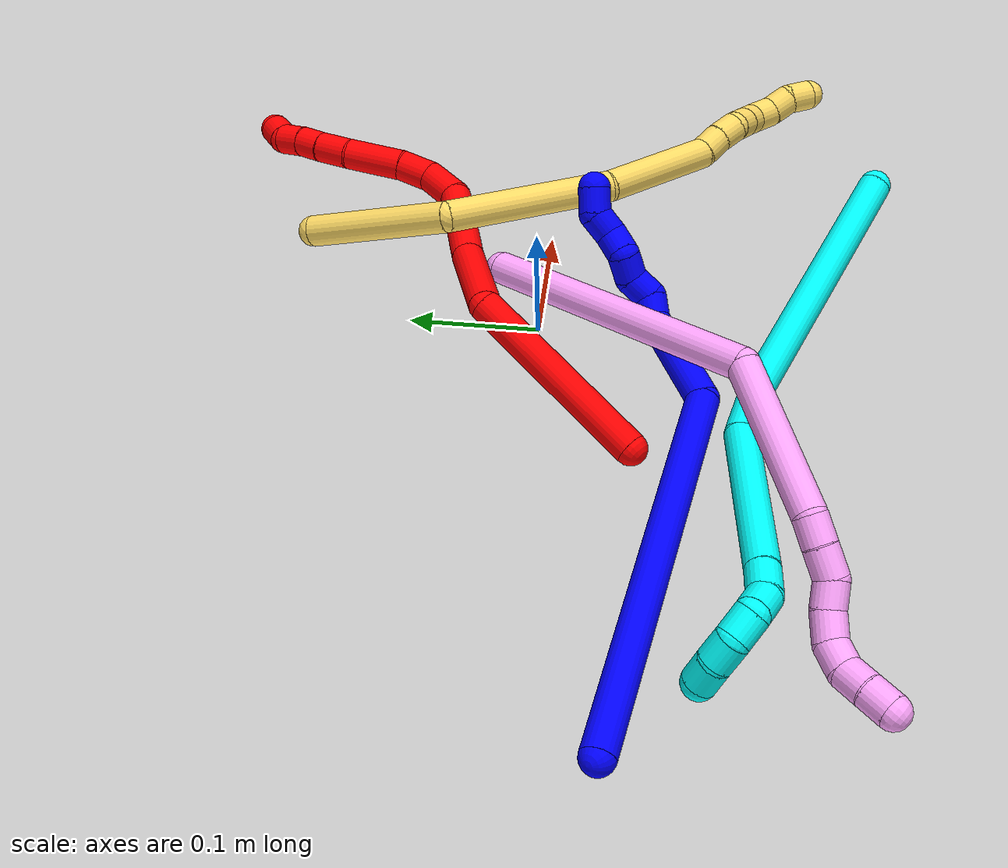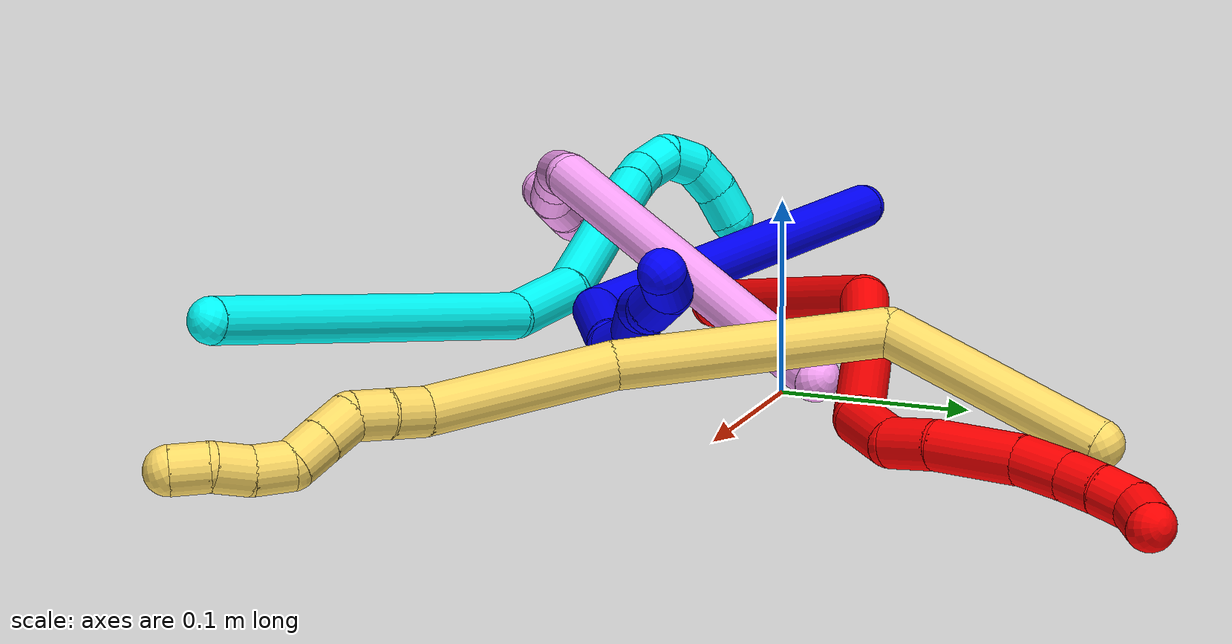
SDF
<sdf version="1.7">
 <world name="default">
  <plugin name="TubeGeneratorPlugin" filename="libtube_generator_plugin.so"/>
  <model name="photoneo_s_sensor">
   <static>1</static>
   <pose>0 0 2 1.57079 1.57079 3.14159</pose>
   <link name="link">
    <inertial><mass>0.1</mass></inertial>
    <sensor name="sensor" type="depth">
     <update_rate>30</update_rate>
     <camera>
      <horizontal_fov>1.22</horizontal_fov>
      <image><width>1920</width><height>1200</height><format>B8G8R8</format></image>
      <clip><near>0.1</near><far>4</far></clip>
      <depth_camera><output>points</output></depth_camera>
     </camera>
     <plugin name="camera_plugin" filename="libgazebo_ros_depth_camera.so">
      <baseline>0.2</baseline>
      <alwaysOn>1</alwaysOn>
      <updateRate>0.0</updateRate>
      <cameraName>camera_ir</cameraName>
      <imageTopicName>/camera/color/image_raw</imageTopicName>
      <cameraInfoTopicName>/camera/color/camera_info</cameraInfoTopicName>
      <depthImageTopicName>/camera/depth/image_raw</depthImageTopicName>
      <depthImageCameraInfoTopicName>/camera/depth/camera_info</depthImageCameraInfoTopicName>
      <pointCloudTopicName>/camera/depth/points</pointCloudTopicName>
      <frameName>fr_optical</frameName>
      <pointCloudCutoff>0.1</pointCloudCutoff>
      <pointCloudCutoffMax>2.0</pointCloudCutoffMax>
      <distortionK1>0</distortionK1>
      <distortionK2>0</distortionK2>
      <distortionK3>0</distortionK3>
      <distortionT1>0</distortionT1>
      <distortionT2>0</distortionT2>
      <CxPrime>0</CxPrime>
      <Cx>0</Cx>
      <Cy>0</Cy>
      <focalLength>0</focalLength>
      <hackBaseline>0</hackBaseline>
     </plugin>
    </sensor>
   </link>
  </model>
  <gravity>0 0 -9.8</gravity>
  <magnetic_field>6e-06 2.3e-05 -4.2e-05</magnetic_field>
  <atmosphere type="adiabatic"/>
  <physics name="default_physics" default="0" type="ode">
   <max_step_size>0.003</max_step_size>
   <real_time_factor>1</real_time_factor>
   <real_time_update_rate>1000</real_time_update_rate>
   <max_contacts>10000</max_contacts>
   <ode>
    <solver>
     <type>quick</type>
     <iters>100</iters>
     <sor>1.3</sor>
     <use_dynamic_moi_rescaling>0</use_dynamic_moi_rescaling>
    </solver>
    <constraints>
     <contact_max_correcting_vel>0</contact_max_correcting_vel>
     <contact_surface_layer>0.001</contact_surface_layer>
     <cfm>0</cfm>
     <erp>0.2</erp>
    </constraints>
   </ode>
  </physics>
  <scene><ambient>0.4 0.4 0.4 1</ambient><background>0.7 0.7 0.7 1</background><shadows>0</shadows></scene>
  <audio><device>default</device></audio>
  <spherical_coordinates>
   <surface_model>EARTH_WGS84</surface_model>
   <latitude_deg>0</latitude_deg>
   <longitude_deg>0</longitude_deg>
   <elevation>0</elevation>
   <heading_deg>0</heading_deg>
  </spherical_coordinates>
  <model name="bin">
   <static>1</static>
   <link name="bottom">
    <collision name="collision-bottom">
     <pose>0 0 -0.01 0 -0 0</pose>
     <geometry><box><size>0.8 0.6 0.02</size></box></geometry>
     <surface>
      <friction><ode><mu>100</mu><mu2>100</mu2></ode></friction>
      <contact><collide_bitmask>65535</collide_bitmask></contact>
     </surface>
    </collision>
   </link>
   <link name="west_wall">
    <collision name="collision-west_wall">
     <pose>-0.41 0 0.1 0 -0 0</pose>
     <geometry><box><size>0.02 0.6 0.2</size></box></geometry>
     <surface>
      <friction><ode><mu>100</mu><mu2>100</mu2></ode></friction>
      <contact><collide_bitmask>65535</collide_bitmask></contact>
     </surface>
    </collision>
   </link>
   <link name="east_wall">
    <collision name="collision-east_wall">
     <pose>0.41 0 0.1 0 -0 0</pose>
     <geometry><box><size>0.02 0.6 0.2</size></box></geometry>
     <surface>
      <friction><ode><mu>100</mu><mu2>100</mu2></ode></friction>
      <contact><collide_bitmask>65535</collide_bitmask></contact>
     </surface>
    </collision>
   </link>
   <link name="south_wall">
    <collision name="collision-south_wall">
     <pose>0 -0.31 0.1 0 -0 0</pose>
     <geometry><box><size>0.8 0.02 0.2</size></box></geometry>
     <surface>
      <friction><ode><mu>100</mu><mu2>100</mu2></ode></friction>
      <contact><collide_bitmask>65535</collide_bitmask></contact>
     </surface>
    </collision>
   </link>
   <link name="north_wall">
    <collision name="collision-north_wall">
     <pose>0 0.31 0.1 0 -0 0</pose>
     <geometry><box><size>0.8 0.02 0.2</size></box></geometry>
     <surface>
      <friction><ode><mu>100</mu><mu2>100</mu2></ode></friction>
      <contact><collide_bitmask>65535</collide_bitmask></contact>
     </surface>
    </collision>
   </link>
  </model>
  <model name="1">
   <static>0</static>
   <link name="1">
    <collision name="collision-cylinder-e_1_1_4">
     <pose>0.072365 0.028467 -0.124202 -2.91628 0.516492 -2.33226</pose>
     <geometry><cylinder><radius>0.0125</radius><length>0.293074</length></cylinder></geometry>
     <surface>
      <friction><ode><mu>1.16</mu><mu2>1.16</mu2><slip1>0</slip1><slip2>0</slip2></ode></friction>
      <contact><ode><kp>1e+06</kp><kd>1</kd><max_vel>0</max_vel><min_depth>0.001</min_depth></ode></contact>
     </surface>
    </collision>
    <visual name="visual-cylinder-e_1_1_4">
     <pose>0.072365 0.028467 -0.124202 -2.91628 0.516492 -2.33226</pose>
     <geometry><cylinder><radius>0.0125</radius><length>0.293074</length></cylinder></geometry>
     <material><ambient>0 0 1 1</ambient></material>
    </visual>
    <collision name="collision-cylinder-e_2_4_5">
     <pose>0.161694 0.080956 -0.264025 -2.14739 0.534547 -0.934808</pose>
     <geometry><cylinder><radius>0.0125</radius><length>0.066599</length></cylinder></geometry>
     <surface>
      <friction><ode><mu>1.16</mu><mu2>1.16</mu2><slip1>0</slip1><slip2>0</slip2></ode></friction>
      <contact><ode><kp>1e+06</kp><kd>1</kd><max_vel>0</max_vel><min_depth>0.001</min_depth></ode></contact>
     </surface>
    </collision>
    <visual name="visual-cylinder-e_2_4_5">
     <pose>0.161694 0.080956 -0.264025 -2.14739 0.534547 -0.934808</pose>
     <geometry><cylinder><radius>0.0125</radius><length>0.066599</length></cylinder></geometry>
     <material><ambient>0 0 1 1</ambient></material>
    </visual>
    <collision name="collision-cylinder-e_3_5_6">
     <pose>0.182088 0.112719 -0.285136 -2.18767 0.346806 -0.653624</pose>
     <geometry><cylinder><radius>0.0125</radius><length>0.020183</length></cylinder></geometry>
     <surface>
      <friction><ode><mu>1.16</mu><mu2>1.16</mu2><slip1>0</slip1><slip2>0</slip2></ode></friction>
      <contact><ode><kp>1e+06</kp><kd>1</kd><max_vel>0</max_vel><min_depth>0.001</min_depth></ode></contact>
     </surface>
    </collision>
    <visual name="visual-cylinder-e_3_5_6">
     <pose>0.182088 0.112719 -0.285136 -2.18767 0.346806 -0.653624</pose>
     <geometry><cylinder><radius>0.0125</radius><length>0.020183</length></cylinder></geometry>
     <material><ambient>0 0 1 1</ambient></material>
    </visual>
    <collision name="collision-cylinder-e_4_6_7">
     <pose>0.194353 0.12378 -0.294014 -2.36628 1.07808 -1.9436</pose>
     <geometry><cylinder><radius>0.0125</radius><length>0.020055</length></cylinder></geometry>
     <surface>
      <friction><ode><mu>1.16</mu><mu2>1.16</mu2><slip1>0</slip1><slip2>0</slip2></ode></friction>
      <contact><ode><kp>1e+06</kp><kd>1</kd><max_vel>0</max_vel><min_depth>0.001</min_depth></ode></contact>
     </surface>
    </collision>
    <visual name="visual-cylinder-e_4_6_7">
     <pose>0.194353 0.12378 -0.294014 -2.36628 1.07808 -1.9436</pose>
     <geometry><cylinder><radius>0.0125</radius><length>0.020055</length></cylinder></geometry>
     <material><ambient>0 0 1 1</ambient></material>
    </visual>
    <collision name="collision-cylinder-e_5_7_8">
     <pose>0.210208 0.133831 -0.294947 -1.221 0.775202 -0.556459</pose>
     <geometry><cylinder><radius>0.0125</radius><length>0.02006</length></cylinder></geometry>
     <surface>
      <friction><ode><mu>1.16</mu><mu2>1.16</mu2><slip1>0</slip1><slip2>0</slip2></ode></friction>
      <contact><ode><kp>1e+06</kp><kd>1</kd><max_vel>0</max_vel><min_depth>0.001</min_depth></ode></contact>
     </surface>
    </collision>
    <visual name="visual-cylinder-e_5_7_8">
     <pose>0.210208 0.133831 -0.294947 -1.221 0.775202 -0.556459</pose>
     <geometry><cylinder><radius>0.0125</radius><length>0.02006</length></cylinder></geometry>
     <material><ambient>0 0 1 1</ambient></material>
    </visual>
    <collision name="collision-cylinder-e_6_8_9">
     <pose>0.226917 0.14236 -0.29072 -0.792971 1.31595 -0.625869</pose>
     <geometry><cylinder><radius>0.0125</radius><length>0.020025</length></cylinder></geometry>
     <surface>
      <friction><ode><mu>1.16</mu><mu2>1.16</mu2><slip1>0</slip1><slip2>0</slip2></ode></friction>
      <contact><ode><kp>1e+06</kp><kd>1</kd><max_vel>0</max_vel><min_depth>0.001</min_depth></ode></contact>
     </surface>
    </collision>
    <visual name="visual-cylinder-e_6_8_9">
     <pose>0.226917 0.14236 -0.29072 -0.792971 1.31595 -0.625869</pose>
     <geometry><cylinder><radius>0.0125</radius><length>0.020025</length></cylinder></geometry>
     <material><ambient>0 0 1 1</ambient></material>
    </visual>
    <collision name="collision-cylinder-e_7_9_10">
     <pose>0.243343 0.151028 -0.291677 -1.94879 0.739014 -1.0369</pose>
     <geometry><cylinder><radius>0.0125</radius><length>0.020003</length></cylinder></geometry>
     <surface>
      <friction><ode><mu>1.16</mu><mu2>1.16</mu2><slip1>0</slip1><slip2>0</slip2></ode></friction>
      <contact><ode><kp>1e+06</kp><kd>1</kd><max_vel>0</max_vel><min_depth>0.001</min_depth></ode></contact>
     </surface>
    </collision>
    <visual name="visual-cylinder-e_7_9_10">
     <pose>0.243343 0.151028 -0.291677 -1.94879 0.739014 -1.0369</pose>
     <geometry><cylinder><radius>0.0125</radius><length>0.020003</length></cylinder></geometry>
     <material><ambient>0 0 1 1</ambient></material>
    </visual>
    <collision name="collision-cylinder-e_8_10_11">
     <pose>0.2582 0.163217 -0.292003 -1.14652 0.947692 -0.639405</pose>
     <geometry><cylinder><radius>0.0125</radius><length>0.02</length></cylinder></geometry>
     <surface>
      <friction><ode><mu>1.16</mu><mu2>1.16</mu2><slip1>0</slip1><slip2>0</slip2></ode></friction>
      <contact><ode><kp>1e+06</kp><kd>1</kd><max_vel>0</max_vel><min_depth>0.001</min_depth></ode></contact>
     </surface>
    </collision>
    <visual name="visual-cylinder-e_8_10_11">
     <pose>0.2582 0.163217 -0.292003 -1.14652 0.947692 -0.639405</pose>
     <geometry><cylinder><radius>0.0125</radius><length>0.02</length></cylinder></geometry>
     <material><ambient>0 0 1 1</ambient></material>
    </visual>
    <collision name="collision-cylinder-e_9_11_2">
     <pose>0.275929 0.169769 -0.292082 -2.68004 1.29001 -2.53618</pose>
     <geometry><cylinder><radius>0.0125</radius><length>0.02</length></cylinder></geometry>
     <surface>
      <friction><ode><mu>1.16</mu><mu2>1.16</mu2><slip1>0</slip1><slip2>0</slip2></ode></friction>
      <contact><ode><kp>1e+06</kp><kd>1</kd><max_vel>0</max_vel><min_depth>0.001</min_depth></ode></contact>
     </surface>
    </collision>
    <visual name="visual-cylinder-e_9_11_2">
     <pose>0.275929 0.169769 -0.292082 -2.68004 1.29001 -2.53618</pose>
     <geometry><cylinder><radius>0.0125</radius><length>0.02</length></cylinder></geometry>
     <material><ambient>0 0 1 1</ambient></material>
    </visual>
    <collision name="collision-sphere-2">
     <pose>0.285538 0.171004 -0.294563 0 -0 0</pose>
     <geometry><sphere><radius>0.0125</radius></sphere></geometry>
     <surface>
      <friction><ode><mu>1.16</mu><mu2>1.16</mu2><slip1>0</slip1><slip2>0</slip2></ode></friction>
      <contact><ode><kp>1e+06</kp><kd>1</kd><max_vel>0</max_vel><min_depth>0.001</min_depth></ode></contact>
     </surface>
    </collision>
    <visual name="visual-sphere-2">
     <pose>0.285538 0.171004 -0.294563 0 -0 0</pose>
     <geometry><sphere><radius>0.0125</radius></sphere></geometry>
     <material><ambient>0 0 1 1</ambient></material>
    </visual>
    <collision name="collision-sphere-11">
     <pose>0.266321 0.168535 -0.289601 0 -0 0</pose>
     <geometry><sphere><radius>0.0125</radius></sphere></geometry>
     <surface>
      <friction><ode><mu>1.16</mu><mu2>1.16</mu2><slip1>0</slip1><slip2>0</slip2></ode></friction>
      <contact><ode><kp>1e+06</kp><kd>1</kd><max_vel>0</max_vel><min_depth>0.001</min_depth></ode></contact>
     </surface>
    </collision>
    <visual name="visual-sphere-11">
     <pose>0.266321 0.168535 -0.289601 0 -0 0</pose>
     <geometry><sphere><radius>0.0125</radius></sphere></geometry>
     <material><ambient>0 0 1 1</ambient></material>
    </visual>
    <collision name="collision-sphere-10">
     <pose>0.250079 0.157899 -0.294405 0 -0 0</pose>
     <geometry><sphere><radius>0.0125</radius></sphere></geometry>
     <surface>
      <friction><ode><mu>1.16</mu><mu2>1.16</mu2><slip1>0</slip1><slip2>0</slip2></ode></friction>
      <contact><ode><kp>1e+06</kp><kd>1</kd><max_vel>0</max_vel><min_depth>0.001</min_depth></ode></contact>
     </surface>
    </collision>
    <visual name="visual-sphere-10">
     <pose>0.250079 0.157899 -0.294405 0 -0 0</pose>
     <geometry><sphere><radius>0.0125</radius></sphere></geometry>
     <material><ambient>0 0 1 1</ambient></material>
    </visual>
    <collision name="collision-sphere-9">
     <pose>0.236606 0.144158 -0.288949 0 -0 0</pose>
     <geometry><sphere><radius>0.0125</radius></sphere></geometry>
     <surface>
      <friction><ode><mu>1.16</mu><mu2>1.16</mu2><slip1>0</slip1><slip2>0</slip2></ode></friction>
      <contact><ode><kp>1e+06</kp><kd>1</kd><max_vel>0</max_vel><min_depth>0.001</min_depth></ode></contact>
     </surface>
    </collision>
    <visual name="visual-sphere-9">
     <pose>0.236606 0.144158 -0.288949 0 -0 0</pose>
     <geometry><sphere><radius>0.0125</radius></sphere></geometry>
     <material><ambient>0 0 1 1</ambient></material>
    </visual>
    <collision name="collision-sphere-4">
     <pose>0.144729 0.056934 -0.248403 0 -0 0</pose>
     <geometry><sphere><radius>0.0125</radius></sphere></geometry>
     <surface>
      <friction><ode><mu>1.16</mu><mu2>1.16</mu2><slip1>0</slip1><slip2>0</slip2></ode></friction>
      <contact><ode><kp>1e+06</kp><kd>1</kd><max_vel>0</max_vel><min_depth>0.001</min_depth></ode></contact>
     </surface>
    </collision>
    <visual name="visual-sphere-4">
     <pose>0.144729 0.056934 -0.248403 0 -0 0</pose>
     <geometry><sphere><radius>0.0125</radius></sphere></geometry>
     <material><ambient>0 0 1 1</ambient></material>
    </visual>
    <collision name="collision-sphere-1">
     <geometry><sphere><radius>0.0125</radius></sphere></geometry>
     <surface>
      <friction><ode><mu>1.16</mu><mu2>1.16</mu2><slip1>0</slip1><slip2>0</slip2></ode></friction>
      <contact><ode><kp>1e+06</kp><kd>1</kd><max_vel>0</max_vel><min_depth>0.001</min_depth></ode></contact>
     </surface>
    </collision>
    <visual name="visual-sphere-1">
     <geometry><sphere><radius>0.0125</radius></sphere></geometry>
     <material><ambient>0 0 1 1</ambient></material>
    </visual>
    <collision name="collision-sphere-8">
     <pose>0.217228 0.140561 -0.292491 0 -0 0</pose>
     <geometry><sphere><radius>0.0125</radius></sphere></geometry>
     <surface>
      <friction><ode><mu>1.16</mu><mu2>1.16</mu2><slip1>0</slip1><slip2>0</slip2></ode></friction>
      <contact><ode><kp>1e+06</kp><kd>1</kd><max_vel>0</max_vel><min_depth>0.001</min_depth></ode></contact>
     </surface>
    </collision>
    <visual name="visual-sphere-8">
     <pose>0.217228 0.140561 -0.292491 0 -0 0</pose>
     <geometry><sphere><radius>0.0125</radius></sphere></geometry>
     <material><ambient>0 0 1 1</ambient></material>
    </visual>
    <collision name="collision-sphere-5">
     <pose>0.178659 0.104978 -0.279646 0 -0 0</pose>
     <geometry><sphere><radius>0.0125</radius></sphere></geometry>
     <surface>
      <friction><ode><mu>1.16</mu><mu2>1.16</mu2><slip1>0</slip1><slip2>0</slip2></ode></friction>
      <contact><ode><kp>1e+06</kp><kd>1</kd><max_vel>0</max_vel><min_depth>0.001</min_depth></ode></contact>
     </surface>
    </collision>
    <visual name="visual-sphere-5">
     <pose>0.178659 0.104978 -0.279646 0 -0 0</pose>
     <geometry><sphere><radius>0.0125</radius></sphere></geometry>
     <material><ambient>0 0 1 1</ambient></material>
    </visual>
    <collision name="collision-sphere-6">
     <pose>0.185518 0.12046 -0.290627 0 -0 0</pose>
     <geometry><sphere><radius>0.0125</radius></sphere></geometry>
     <surface>
      <friction><ode><mu>1.16</mu><mu2>1.16</mu2><slip1>0</slip1><slip2>0</slip2></ode></friction>
      <contact><ode><kp>1e+06</kp><kd>1</kd><max_vel>0</max_vel><min_depth>0.001</min_depth></ode></contact>
     </surface>
    </collision>
    <visual name="visual-sphere-6">
     <pose>0.185518 0.12046 -0.290627 0 -0 0</pose>
     <geometry><sphere><radius>0.0125</radius></sphere></geometry>
     <material><ambient>0 0 1 1</ambient></material>
    </visual>
    <collision name="collision-sphere-7">
     <pose>0.203188 0.1271 -0.297402 0 -0 0</pose>
     <geometry><sphere><radius>0.0125</radius></sphere></geometry>
     <surface>
      <friction><ode><mu>1.16</mu><mu2>1.16</mu2><slip1>0</slip1><slip2>0</slip2></ode></friction>
      <contact><ode><kp>1e+06</kp><kd>1</kd><max_vel>0</max_vel><min_depth>0.001</min_depth></ode></contact>
     </surface>
    </collision>
    <visual name="visual-sphere-7">
     <pose>0.203188 0.1271 -0.297402 0 -0 0</pose>
     <geometry><sphere><radius>0.0125</radius></sphere></geometry>
     <material><ambient>0 0 1 1</ambient></material>
    </visual>
    <inertial>
     <pose>0.127722 0.067417 -0.18978 0 -0 0</pose>
     <mass>0.5</mass>
     <inertia>
      <ixx>-0.002577</ixx>
      <ixy>0</ixy>
      <ixz>0</ixz>
      <iyy>0.000257</iyy>
      <iyz>0</iyz>
      <izz>-0.00152</izz>
     </inertia>
    </inertial>
   </link>
   <pose>-0.356738 -0.078107 0.012285 -0.678348 -1.01752 0.217203</pose>
  </model>
  <model name="2">
   <static>0</static>
   <link name="2">
    <collision name="collision-cylinder-e_1_1_4">
     <pose>-0.000426 9.1e-05 0.077282 -0.001178 -0.005506 3e-06</pose>
     <geometry><cylinder><radius>0.0125</radius><length>0.154567</length></cylinder></geometry>
     <surface>
      <friction><ode><mu>1.16</mu><mu2>1.16</mu2><slip1>0</slip1><slip2>0</slip2></ode></friction>
      <contact><ode><kp>1e+06</kp><kd>1</kd><max_vel>0</max_vel><min_depth>0.001</min_depth></ode></contact>
     </surface>
    </collision>
    <visual name="visual-cylinder-e_1_1_4">
     <pose>-0.000426 9.1e-05 0.077282 -0.001178 -0.005506 3e-06</pose>
     <geometry><cylinder><radius>0.0125</radius><length>0.154567</length></cylinder></geometry>
     <material><ambient>1 0 0 1</ambient></material>
    </visual>
    <collision name="collision-cylinder-e_2_4_5">
     <pose>0.020377 0.009594 0.181694 -0.333948 0.636598 -0.110957</pose>
     <geometry><cylinder><radius>0.0125</radius><length>0.071421</length></cylinder></geometry>
     <surface>
      <friction><ode><mu>1.16</mu><mu2>1.16</mu2><slip1>0</slip1><slip2>0</slip2></ode></friction>
      <contact><ode><kp>1e+06</kp><kd>1</kd><max_vel>0</max_vel><min_depth>0.001</min_depth></ode></contact>
     </surface>
    </collision>
    <visual name="visual-cylinder-e_2_4_5">
     <pose>0.020377 0.009594 0.181694 -0.333948 0.636598 -0.110957</pose>
     <geometry><cylinder><radius>0.0125</radius><length>0.071421</length></cylinder></geometry>
     <material><ambient>1 0 0 1</ambient></material>
    </visual>
    <collision name="collision-cylinder-e_3_5_6">
     <pose>0.065518 0.023317 0.239145 -0.14121 0.662898 -0.048668</pose>
     <geometry><cylinder><radius>0.0125</radius><length>0.077713</length></cylinder></geometry>
     <surface>
      <friction><ode><mu>1.16</mu><mu2>1.16</mu2><slip1>0</slip1><slip2>0</slip2></ode></friction>
      <contact><ode><kp>1e+06</kp><kd>1</kd><max_vel>0</max_vel><min_depth>0.001</min_depth></ode></contact>
     </surface>
    </collision>
    <visual name="visual-cylinder-e_3_5_6">
     <pose>0.065518 0.023317 0.239145 -0.14121 0.662898 -0.048668</pose>
     <geometry><cylinder><radius>0.0125</radius><length>0.077713</length></cylinder></geometry>
     <material><ambient>1 0 0 1</ambient></material>
    </visual>
    <collision name="collision-cylinder-e_4_6_7">
     <pose>0.092435 0.032418 0.286077 -0.280801 0.172075 -0.024378</pose>
     <geometry><cylinder><radius>0.0125</radius><length>0.035092</length></cylinder></geometry>
     <surface>
      <friction><ode><mu>1.16</mu><mu2>1.16</mu2><slip1>0</slip1><slip2>0</slip2></ode></friction>
      <contact><ode><kp>1e+06</kp><kd>1</kd><max_vel>0</max_vel><min_depth>0.001</min_depth></ode></contact>
     </surface>
    </collision>
    <visual name="visual-cylinder-e_4_6_7">
     <pose>0.092435 0.032418 0.286077 -0.280801 0.172075 -0.024378</pose>
     <geometry><cylinder><radius>0.0125</radius><length>0.035092</length></cylinder></geometry>
     <material><ambient>1 0 0 1</ambient></material>
    </visual>
    <collision name="collision-cylinder-e_5_7_8">
     <pose>0.090829 0.039699 0.314906 -0.201072 -0.35412 0.036096</pose>
     <geometry><cylinder><radius>0.0125</radius><length>0.02659</length></cylinder></geometry>
     <surface>
      <friction><ode><mu>1.16</mu><mu2>1.16</mu2><slip1>0</slip1><slip2>0</slip2></ode></friction>
      <contact><ode><kp>1e+06</kp><kd>1</kd><max_vel>0</max_vel><min_depth>0.001</min_depth></ode></contact>
     </surface>
    </collision>
    <visual name="visual-cylinder-e_5_7_8">
     <pose>0.090829 0.039699 0.314906 -0.201072 -0.35412 0.036096</pose>
     <geometry><cylinder><radius>0.0125</radius><length>0.02659</length></cylinder></geometry>
     <material><ambient>1 0 0 1</ambient></material>
    </visual>
    <collision name="collision-cylinder-e_6_8_9">
     <pose>0.077091 0.049874 0.347375 -0.362679 -0.398844 0.074081</pose>
     <geometry><cylinder><radius>0.0125</radius><length>0.047007</length></cylinder></geometry>
     <surface>
      <friction><ode><mu>1.16</mu><mu2>1.16</mu2><slip1>0</slip1><slip2>0</slip2></ode></friction>
      <contact><ode><kp>1e+06</kp><kd>1</kd><max_vel>0</max_vel><min_depth>0.001</min_depth></ode></contact>
     </surface>
    </collision>
    <visual name="visual-cylinder-e_6_8_9">
     <pose>0.077091 0.049874 0.347375 -0.362679 -0.398844 0.074081</pose>
     <geometry><cylinder><radius>0.0125</radius><length>0.047007</length></cylinder></geometry>
     <material><ambient>1 0 0 1</ambient></material>
    </visual>
    <collision name="collision-cylinder-e_7_9_10">
     <pose>0.064751 0.062963 0.379706 -0.420643 -0.238101 0.05106</pose>
     <geometry><cylinder><radius>0.0125</radius><length>0.027239</length></cylinder></geometry>
     <surface>
      <friction><ode><mu>1.16</mu><mu2>1.16</mu2><slip1>0</slip1><slip2>0</slip2></ode></friction>
      <contact><ode><kp>1e+06</kp><kd>1</kd><max_vel>0</max_vel><min_depth>0.001</min_depth></ode></contact>
     </surface>
    </collision>
    <visual name="visual-cylinder-e_7_9_10">
     <pose>0.064751 0.062963 0.379706 -0.420643 -0.238101 0.05106</pose>
     <geometry><cylinder><radius>0.0125</radius><length>0.027239</length></cylinder></geometry>
     <material><ambient>1 0 0 1</ambient></material>
    </visual>
    <collision name="collision-cylinder-e_8_10_11">
     <pose>0.059912 0.072309 0.400885 -0.408846 -0.162604 0.033782</pose>
     <geometry><cylinder><radius>0.0125</radius><length>0.020094</length></cylinder></geometry>
     <surface>
      <friction><ode><mu>1.16</mu><mu2>1.16</mu2><slip1>0</slip1><slip2>0</slip2></ode></friction>
      <contact><ode><kp>1e+06</kp><kd>1</kd><max_vel>0</max_vel><min_depth>0.001</min_depth></ode></contact>
     </surface>
    </collision>
    <visual name="visual-cylinder-e_8_10_11">
     <pose>0.059912 0.072309 0.400885 -0.408846 -0.162604 0.033782</pose>
     <geometry><cylinder><radius>0.0125</radius><length>0.020094</length></cylinder></geometry>
     <material><ambient>1 0 0 1</ambient></material>
    </visual>
    <collision name="collision-cylinder-e_9_11_12">
     <pose>0.056195 0.081206 0.418522 -0.525785 -0.20869 0.056353</pose>
     <geometry><cylinder><radius>0.0125</radius><length>0.020185</length></cylinder></geometry>
     <surface>
      <friction><ode><mu>1.16</mu><mu2>1.16</mu2><slip1>0</slip1><slip2>0</slip2></ode></friction>
      <contact><ode><kp>1e+06</kp><kd>1</kd><max_vel>0</max_vel><min_depth>0.001</min_depth></ode></contact>
     </surface>
    </collision>
    <visual name="visual-cylinder-e_9_11_12">
     <pose>0.056195 0.081206 0.418522 -0.525785 -0.20869 0.056353</pose>
     <geometry><cylinder><radius>0.0125</radius><length>0.020185</length></cylinder></geometry>
     <material><ambient>1 0 0 1</ambient></material>
    </visual>
    <collision name="collision-cylinder-e_10_12_2">
     <pose>0.057518 0.089397 0.435939 -0.349508 0.346745 -0.061821</pose>
     <geometry><cylinder><radius>0.0125</radius><length>0.020092</length></cylinder></geometry>
     <surface>
      <friction><ode><mu>1.16</mu><mu2>1.16</mu2><slip1>0</slip1><slip2>0</slip2></ode></friction>
      <contact><ode><kp>1e+06</kp><kd>1</kd><max_vel>0</max_vel><min_depth>0.001</min_depth></ode></contact>
     </surface>
    </collision>
    <visual name="visual-cylinder-e_10_12_2">
     <pose>0.057518 0.089397 0.435939 -0.349508 0.346745 -0.061821</pose>
     <geometry><cylinder><radius>0.0125</radius><length>0.020092</length></cylinder></geometry>
     <material><ambient>1 0 0 1</ambient></material>
    </visual>
    <collision name="collision-sphere-2">
     <pose>0.060932 0.092632 0.444816 0 -0 0</pose>
     <geometry><sphere><radius>0.0125</radius></sphere></geometry>
     <surface>
      <friction><ode><mu>1.16</mu><mu2>1.16</mu2><slip1>0</slip1><slip2>0</slip2></ode></friction>
      <contact><ode><kp>1e+06</kp><kd>1</kd><max_vel>0</max_vel><min_depth>0.001</min_depth></ode></contact>
     </surface>
    </collision>
    <visual name="visual-sphere-2">
     <pose>0.060932 0.092632 0.444816 0 -0 0</pose>
     <geometry><sphere><radius>0.0125</radius></sphere></geometry>
     <material><ambient>1 0 0 1</ambient></material>
    </visual>
    <collision name="collision-sphere-12">
     <pose>0.054104 0.086161 0.427062 0 -0 0</pose>
     <geometry><sphere><radius>0.0125</radius></sphere></geometry>
     <surface>
      <friction><ode><mu>1.16</mu><mu2>1.16</mu2><slip1>0</slip1><slip2>0</slip2></ode></friction>
      <contact><ode><kp>1e+06</kp><kd>1</kd><max_vel>0</max_vel><min_depth>0.001</min_depth></ode></contact>
     </surface>
    </collision>
    <visual name="visual-sphere-12">
     <pose>0.054104 0.086161 0.427062 0 -0 0</pose>
     <geometry><sphere><radius>0.0125</radius></sphere></geometry>
     <material><ambient>1 0 0 1</ambient></material>
    </visual>
    <collision name="collision-sphere-11">
     <pose>0.058286 0.076251 0.409983 0 -0 0</pose>
     <geometry><sphere><radius>0.0125</radius></sphere></geometry>
     <surface>
      <friction><ode><mu>1.16</mu><mu2>1.16</mu2><slip1>0</slip1><slip2>0</slip2></ode></friction>
      <contact><ode><kp>1e+06</kp><kd>1</kd><max_vel>0</max_vel><min_depth>0.001</min_depth></ode></contact>
     </surface>
    </collision>
    <visual name="visual-sphere-11">
     <pose>0.058286 0.076251 0.409983 0 -0 0</pose>
     <geometry><sphere><radius>0.0125</radius></sphere></geometry>
     <material><ambient>1 0 0 1</ambient></material>
    </visual>
    <collision name="collision-sphere-10">
     <pose>0.061539 0.068368 0.391788 0 -0 0</pose>
     <geometry><sphere><radius>0.0125</radius></sphere></geometry>
     <surface>
      <friction><ode><mu>1.16</mu><mu2>1.16</mu2><slip1>0</slip1><slip2>0</slip2></ode></friction>
      <contact><ode><kp>1e+06</kp><kd>1</kd><max_vel>0</max_vel><min_depth>0.001</min_depth></ode></contact>
     </surface>
    </collision>
    <visual name="visual-sphere-10">
     <pose>0.061539 0.068368 0.391788 0 -0 0</pose>
     <geometry><sphere><radius>0.0125</radius></sphere></geometry>
     <material><ambient>1 0 0 1</ambient></material>
    </visual>
    <collision name="collision-sphere-9">
     <pose>0.067964 0.057558 0.367625 0 -0 0</pose>
     <geometry><sphere><radius>0.0125</radius></sphere></geometry>
     <surface>
      <friction><ode><mu>1.16</mu><mu2>1.16</mu2><slip1>0</slip1><slip2>0</slip2></ode></friction>
      <contact><ode><kp>1e+06</kp><kd>1</kd><max_vel>0</max_vel><min_depth>0.001</min_depth></ode></contact>
     </surface>
    </collision>
    <visual name="visual-sphere-9">
     <pose>0.067964 0.057558 0.367625 0 -0 0</pose>
     <geometry><sphere><radius>0.0125</radius></sphere></geometry>
     <material><ambient>1 0 0 1</ambient></material>
    </visual>
    <collision name="collision-sphere-4">
     <pose>-0.000851 0.000182 0.154565 0 -0 0</pose>
     <geometry><sphere><radius>0.0125</radius></sphere></geometry>
     <surface>
      <friction><ode><mu>1.16</mu><mu2>1.16</mu2><slip1>0</slip1><slip2>0</slip2></ode></friction>
      <contact><ode><kp>1e+06</kp><kd>1</kd><max_vel>0</max_vel><min_depth>0.001</min_depth></ode></contact>
     </surface>
    </collision>
    <visual name="visual-sphere-4">
     <pose>-0.000851 0.000182 0.154565 0 -0 0</pose>
     <geometry><sphere><radius>0.0125</radius></sphere></geometry>
     <material><ambient>1 0 0 1</ambient></material>
    </visual>
    <collision name="collision-sphere-1">
     <geometry><sphere><radius>0.0125</radius></sphere></geometry>
     <surface>
      <friction><ode><mu>1.16</mu><mu2>1.16</mu2><slip1>0</slip1><slip2>0</slip2></ode></friction>
      <contact><ode><kp>1e+06</kp><kd>1</kd><max_vel>0</max_vel><min_depth>0.001</min_depth></ode></contact>
     </surface>
    </collision>
    <visual name="visual-sphere-1">
     <geometry><sphere><radius>0.0125</radius></sphere></geometry>
     <material><ambient>1 0 0 1</ambient></material>
    </visual>
    <collision name="collision-sphere-8">
     <pose>0.086219 0.04219 0.327125 0 -0 0</pose>
     <geometry><sphere><radius>0.0125</radius></sphere></geometry>
     <surface>
      <friction><ode><mu>1.16</mu><mu2>1.16</mu2><slip1>0</slip1><slip2>0</slip2></ode></friction>
      <contact><ode><kp>1e+06</kp><kd>1</kd><max_vel>0</max_vel><min_depth>0.001</min_depth></ode></contact>
     </surface>
    </collision>
    <visual name="visual-sphere-8">
     <pose>0.086219 0.04219 0.327125 0 -0 0</pose>
     <geometry><sphere><radius>0.0125</radius></sphere></geometry>
     <material><ambient>1 0 0 1</ambient></material>
    </visual>
    <collision name="collision-sphere-5">
     <pose>0.041606 0.019007 0.208823 0 -0 0</pose>
     <geometry><sphere><radius>0.0125</radius></sphere></geometry>
     <surface>
      <friction><ode><mu>1.16</mu><mu2>1.16</mu2><slip1>0</slip1><slip2>0</slip2></ode></friction>
      <contact><ode><kp>1e+06</kp><kd>1</kd><max_vel>0</max_vel><min_depth>0.001</min_depth></ode></contact>
     </surface>
    </collision>
    <visual name="visual-sphere-5">
     <pose>0.041606 0.019007 0.208823 0 -0 0</pose>
     <geometry><sphere><radius>0.0125</radius></sphere></geometry>
     <material><ambient>1 0 0 1</ambient></material>
    </visual>
    <collision name="collision-sphere-6">
     <pose>0.089431 0.027628 0.269467 0 -0 0</pose>
     <geometry><sphere><radius>0.0125</radius></sphere></geometry>
     <surface>
      <friction><ode><mu>1.16</mu><mu2>1.16</mu2><slip1>0</slip1><slip2>0</slip2></ode></friction>
      <contact><ode><kp>1e+06</kp><kd>1</kd><max_vel>0</max_vel><min_depth>0.001</min_depth></ode></contact>
     </surface>
    </collision>
    <visual name="visual-sphere-6">
     <pose>0.089431 0.027628 0.269467 0 -0 0</pose>
     <geometry><sphere><radius>0.0125</radius></sphere></geometry>
     <material><ambient>1 0 0 1</ambient></material>
    </visual>
    <collision name="collision-sphere-7">
     <pose>0.095439 0.037209 0.302687 0 -0 0</pose>
     <geometry><sphere><radius>0.0125</radius></sphere></geometry>
     <surface>
      <friction><ode><mu>1.16</mu><mu2>1.16</mu2><slip1>0</slip1><slip2>0</slip2></ode></friction>
      <contact><ode><kp>1e+06</kp><kd>1</kd><max_vel>0</max_vel><min_depth>0.001</min_depth></ode></contact>
     </surface>
    </collision>
    <visual name="visual-sphere-7">
     <pose>0.095439 0.037209 0.302687 0 -0 0</pose>
     <geometry><sphere><radius>0.0125</radius></sphere></geometry>
     <material><ambient>1 0 0 1</ambient></material>
    </visual>
    <inertial>
     <pose>0.042043 0.027305 0.227706 0 -0 0</pose>
     <mass>0.5</mass>
     <inertia>
      <ixx>0.000398</ixx>
      <ixy>0</ixy>
      <ixz>0</ixz>
      <iyy>0.000415</iyy>
      <iyz>0</iyz>
      <izz>-2.6e-05</izz>
     </inertia>
    </inertial>
   </link>
   <pose>-0.116688 -0.079748 0.011496 -1.32899 0.265614 -0.624687</pose>
  </model>
  <model name="3">
   <static>0</static>
   <link name="3">
    <collision name="collision-cylinder-e_1_1_4">
     <pose>-0.014476 0.036827 -0.098389 -2.78344 -0.136928 0.724216</pose>
     <geometry><cylinder><radius>0.0125</radius><length>0.212096</length></cylinder></geometry>
     <surface>
      <friction><ode><mu>1.16</mu><mu2>1.16</mu2><slip1>0</slip1><slip2>0</slip2></ode></friction>
      <contact><ode><kp>1e+06</kp><kd>1</kd><max_vel>0</max_vel><min_depth>0.001</min_depth></ode></contact>
     </surface>
    </collision>
    <visual name="visual-cylinder-e_1_1_4">
     <pose>-0.014476 0.036827 -0.098389 -2.78344 -0.136928 0.724216</pose>
     <geometry><cylinder><radius>0.0125</radius><length>0.212096</length></cylinder></geometry>
     <material><ambient>0.003922 1 0.996078 1</ambient></material>
    </visual>
    <collision name="collision-cylinder-e_2_4_5">
     <pose>-0.03817 0.086415 -0.216389 -2.5647 -0.375324 1.1386</pose>
     <geometry><cylinder><radius>0.0125</radius><length>0.050295</length></cylinder></geometry>
     <surface>
      <friction><ode><mu>1.16</mu><mu2>1.16</mu2><slip1>0</slip1><slip2>0</slip2></ode></friction>
      <contact><ode><kp>1e+06</kp><kd>1</kd><max_vel>0</max_vel><min_depth>0.001</min_depth></ode></contact>
     </surface>
    </collision>
    <visual name="visual-cylinder-e_2_4_5">
     <pose>-0.03817 0.086415 -0.216389 -2.5647 -0.375324 1.1386</pose>
     <geometry><cylinder><radius>0.0125</radius><length>0.050295</length></cylinder></geometry>
     <material><ambient>0.003922 1 0.996078 1</ambient></material>
    </visual>
    <collision name="collision-cylinder-e_3_5_6">
     <pose>-0.091553 0.13115 -0.275332 -2.45905 -0.716722 1.62386</pose>
     <geometry><cylinder><radius>0.0125</radius><length>0.134461</length></cylinder></geometry>
     <surface>
      <friction><ode><mu>1.16</mu><mu2>1.16</mu2><slip1>0</slip1><slip2>0</slip2></ode></friction>
      <contact><ode><kp>1e+06</kp><kd>1</kd><max_vel>0</max_vel><min_depth>0.001</min_depth></ode></contact>
     </surface>
    </collision>
    <visual name="visual-cylinder-e_3_5_6">
     <pose>-0.091553 0.13115 -0.275332 -2.45905 -0.716722 1.62386</pose>
     <geometry><cylinder><radius>0.0125</radius><length>0.134461</length></cylinder></geometry>
     <material><ambient>0.003922 1 0.996078 1</ambient></material>
    </visual>
    <collision name="collision-cylinder-e_4_6_7">
     <pose>-0.142789 0.168452 -0.321842 -2.50282 -0.669277 1.62092</pose>
     <geometry><cylinder><radius>0.0125</radius><length>0.022796</length></cylinder></geometry>
     <surface>
      <friction><ode><mu>1.16</mu><mu2>1.16</mu2><slip1>0</slip1><slip2>0</slip2></ode></friction>
      <contact><ode><kp>1e+06</kp><kd>1</kd><max_vel>0</max_vel><min_depth>0.001</min_depth></ode></contact>
     </surface>
    </collision>
    <visual name="visual-cylinder-e_4_6_7">
     <pose>-0.142789 0.168452 -0.321842 -2.50282 -0.669277 1.62092</pose>
     <geometry><cylinder><radius>0.0125</radius><length>0.022796</length></cylinder></geometry>
     <material><ambient>0.003922 1 0.996078 1</ambient></material>
    </visual>
    <collision name="collision-cylinder-e_5_7_8">
     <pose>-0.151914 0.181188 -0.335676 -2.30299 -0.203378 0.450098</pose>
     <geometry><cylinder><radius>0.0125</radius><length>0.020335</length></cylinder></geometry>
     <surface>
      <friction><ode><mu>1.16</mu><mu2>1.16</mu2><slip1>0</slip1><slip2>0</slip2></ode></friction>
      <contact><ode><kp>1e+06</kp><kd>1</kd><max_vel>0</max_vel><min_depth>0.001</min_depth></ode></contact>
     </surface>
    </collision>
    <visual name="visual-cylinder-e_5_7_8">
     <pose>-0.151914 0.181188 -0.335676 -2.30299 -0.203378 0.450098</pose>
     <geometry><cylinder><radius>0.0125</radius><length>0.020335</length></cylinder></geometry>
     <material><ambient>0.003922 1 0.996078 1</ambient></material>
    </visual>
    <collision name="collision-cylinder-e_6_8_9">
     <pose>-0.152918 0.190322 -0.352129 -2.96698 0.10515 -1.08263</pose>
     <geometry><cylinder><radius>0.0125</radius><length>0.020005</length></cylinder></geometry>
     <surface>
      <friction><ode><mu>1.16</mu><mu2>1.16</mu2><slip1>0</slip1><slip2>0</slip2></ode></friction>
      <contact><ode><kp>1e+06</kp><kd>1</kd><max_vel>0</max_vel><min_depth>0.001</min_depth></ode></contact>
     </surface>
    </collision>
    <visual name="visual-cylinder-e_6_8_9">
     <pose>-0.152918 0.190322 -0.352129 -2.96698 0.10515 -1.08263</pose>
     <geometry><cylinder><radius>0.0125</radius><length>0.020005</length></cylinder></geometry>
     <material><ambient>0.003922 1 0.996078 1</ambient></material>
    </visual>
    <collision name="collision-cylinder-e_7_9_10">
     <pose>-0.148835 0.189132 -0.371001 2.83057 0.308027 1.56096</pose>
     <geometry><cylinder><radius>0.0125</radius><length>0.02001</length></cylinder></geometry>
     <surface>
      <friction><ode><mu>1.16</mu><mu2>1.16</mu2><slip1>0</slip1><slip2>0</slip2></ode></friction>
      <contact><ode><kp>1e+06</kp><kd>1</kd><max_vel>0</max_vel><min_depth>0.001</min_depth></ode></contact>
     </surface>
    </collision>
    <visual name="visual-cylinder-e_7_9_10">
     <pose>-0.148835 0.189132 -0.371001 2.83057 0.308027 1.56096</pose>
     <geometry><cylinder><radius>0.0125</radius><length>0.02001</length></cylinder></geometry>
     <material><ambient>0.003922 1 0.996078 1</ambient></material>
    </visual>
    <collision name="collision-cylinder-e_8_10_2">
     <pose>-0.142404 0.181301 -0.388099 2.59203 0.34663 1.11146</pose>
     <geometry><cylinder><radius>0.0125</radius><length>0.020002</length></cylinder></geometry>
     <surface>
      <friction><ode><mu>1.16</mu><mu2>1.16</mu2><slip1>0</slip1><slip2>0</slip2></ode></friction>
      <contact><ode><kp>1e+06</kp><kd>1</kd><max_vel>0</max_vel><min_depth>0.001</min_depth></ode></contact>
     </surface>
    </collision>
    <visual name="visual-cylinder-e_8_10_2">
     <pose>-0.142404 0.181301 -0.388099 2.59203 0.34663 1.11146</pose>
     <geometry><cylinder><radius>0.0125</radius><length>0.020002</length></cylinder></geometry>
     <material><ambient>0.003922 1 0.996078 1</ambient></material>
    </visual>
    <collision name="collision-sphere-2">
     <pose>-0.139006 0.176388 -0.39612 0 -0 0</pose>
     <geometry><sphere><radius>0.0125</radius></sphere></geometry>
     <surface>
      <friction><ode><mu>1.16</mu><mu2>1.16</mu2><slip1>0</slip1><slip2>0</slip2></ode></friction>
      <contact><ode><kp>1e+06</kp><kd>1</kd><max_vel>0</max_vel><min_depth>0.001</min_depth></ode></contact>
     </surface>
    </collision>
    <visual name="visual-sphere-2">
     <pose>-0.139006 0.176388 -0.39612 0 -0 0</pose>
     <geometry><sphere><radius>0.0125</radius></sphere></geometry>
     <material><ambient>0.003922 1 0.996078 1</ambient></material>
    </visual>
    <collision name="collision-sphere-10">
     <pose>-0.145802 0.186214 -0.380078 0 -0 0</pose>
     <geometry><sphere><radius>0.0125</radius></sphere></geometry>
     <surface>
      <friction><ode><mu>1.16</mu><mu2>1.16</mu2><slip1>0</slip1><slip2>0</slip2></ode></friction>
      <contact><ode><kp>1e+06</kp><kd>1</kd><max_vel>0</max_vel><min_depth>0.001</min_depth></ode></contact>
     </surface>
    </collision>
    <visual name="visual-sphere-10">
     <pose>-0.145802 0.186214 -0.380078 0 -0 0</pose>
     <geometry><sphere><radius>0.0125</radius></sphere></geometry>
     <material><ambient>0.003922 1 0.996078 1</ambient></material>
    </visual>
    <collision name="collision-sphere-9">
     <pose>-0.151868 0.19205 -0.361925 0 -0 0</pose>
     <geometry><sphere><radius>0.0125</radius></sphere></geometry>
     <surface>
      <friction><ode><mu>1.16</mu><mu2>1.16</mu2><slip1>0</slip1><slip2>0</slip2></ode></friction>
      <contact><ode><kp>1e+06</kp><kd>1</kd><max_vel>0</max_vel><min_depth>0.001</min_depth></ode></contact>
     </surface>
    </collision>
    <visual name="visual-sphere-9">
     <pose>-0.151868 0.19205 -0.361925 0 -0 0</pose>
     <geometry><sphere><radius>0.0125</radius></sphere></geometry>
     <material><ambient>0.003922 1 0.996078 1</ambient></material>
    </visual>
    <collision name="collision-sphere-4">
     <pose>-0.028951 0.073654 -0.196778 0 -0 0</pose>
     <geometry><sphere><radius>0.0125</radius></sphere></geometry>
     <surface>
      <friction><ode><mu>1.16</mu><mu2>1.16</mu2><slip1>0</slip1><slip2>0</slip2></ode></friction>
      <contact><ode><kp>1e+06</kp><kd>1</kd><max_vel>0</max_vel><min_depth>0.001</min_depth></ode></contact>
     </surface>
    </collision>
    <visual name="visual-sphere-4">
     <pose>-0.028951 0.073654 -0.196778 0 -0 0</pose>
     <geometry><sphere><radius>0.0125</radius></sphere></geometry>
     <material><ambient>0.003922 1 0.996078 1</ambient></material>
    </visual>
    <collision name="collision-sphere-1">
     <geometry><sphere><radius>0.0125</radius></sphere></geometry>
     <surface>
      <friction><ode><mu>1.16</mu><mu2>1.16</mu2><slip1>0</slip1><slip2>0</slip2></ode></friction>
      <contact><ode><kp>1e+06</kp><kd>1</kd><max_vel>0</max_vel><min_depth>0.001</min_depth></ode></contact>
     </surface>
    </collision>
    <visual name="visual-sphere-1">
     <geometry><sphere><radius>0.0125</radius></sphere></geometry>
     <material><ambient>0.003922 1 0.996078 1</ambient></material>
    </visual>
    <collision name="collision-sphere-8">
     <pose>-0.153968 0.188594 -0.342332 0 -0 0</pose>
     <geometry><sphere><radius>0.0125</radius></sphere></geometry>
     <surface>
      <friction><ode><mu>1.16</mu><mu2>1.16</mu2><slip1>0</slip1><slip2>0</slip2></ode></friction>
      <contact><ode><kp>1e+06</kp><kd>1</kd><max_vel>0</max_vel><min_depth>0.001</min_depth></ode></contact>
     </surface>
    </collision>
    <visual name="visual-sphere-8">
     <pose>-0.153968 0.188594 -0.342332 0 -0 0</pose>
     <geometry><sphere><radius>0.0125</radius></sphere></geometry>
     <material><ambient>0.003922 1 0.996078 1</ambient></material>
    </visual>
    <collision name="collision-sphere-5">
     <pose>-0.047388 0.099176 -0.235999 0 -0 0</pose>
     <geometry><sphere><radius>0.0125</radius></sphere></geometry>
     <surface>
      <friction><ode><mu>1.16</mu><mu2>1.16</mu2><slip1>0</slip1><slip2>0</slip2></ode></friction>
      <contact><ode><kp>1e+06</kp><kd>1</kd><max_vel>0</max_vel><min_depth>0.001</min_depth></ode></contact>
     </surface>
    </collision>
    <visual name="visual-sphere-5">
     <pose>-0.047388 0.099176 -0.235999 0 -0 0</pose>
     <geometry><sphere><radius>0.0125</radius></sphere></geometry>
     <material><ambient>0.003922 1 0.996078 1</ambient></material>
    </visual>
    <collision name="collision-sphere-6">
     <pose>-0.135718 0.163123 -0.314666 0 -0 0</pose>
     <geometry><sphere><radius>0.0125</radius></sphere></geometry>
     <surface>
      <friction><ode><mu>1.16</mu><mu2>1.16</mu2><slip1>0</slip1><slip2>0</slip2></ode></friction>
      <contact><ode><kp>1e+06</kp><kd>1</kd><max_vel>0</max_vel><min_depth>0.001</min_depth></ode></contact>
     </surface>
    </collision>
    <visual name="visual-sphere-6">
     <pose>-0.135718 0.163123 -0.314666 0 -0 0</pose>
     <geometry><sphere><radius>0.0125</radius></sphere></geometry>
     <material><ambient>0.003922 1 0.996078 1</ambient></material>
    </visual>
    <collision name="collision-sphere-7">
     <pose>-0.149861 0.173782 -0.329019 0 -0 0</pose>
     <geometry><sphere><radius>0.0125</radius></sphere></geometry>
     <surface>
      <friction><ode><mu>1.16</mu><mu2>1.16</mu2><slip1>0</slip1><slip2>0</slip2></ode></friction>
      <contact><ode><kp>1e+06</kp><kd>1</kd><max_vel>0</max_vel><min_depth>0.001</min_depth></ode></contact>
     </surface>
    </collision>
    <visual name="visual-sphere-7">
     <pose>-0.149861 0.173782 -0.329019 0 -0 0</pose>
     <geometry><sphere><radius>0.0125</radius></sphere></geometry>
     <material><ambient>0.003922 1 0.996078 1</ambient></material>
    </visual>
    <inertial>
     <pose>-0.06506 0.097069 -0.210332 0 -0 0</pose>
     <mass>0.5</mass>
     <inertia>
      <ixx>0.001282</ixx>
      <ixy>0</ixy>
      <ixz>0</ixz>
      <iyy>0.000265</iyy>
      <iyz>0</iyz>
      <izz>-0.000165</izz>
     </inertia>
    </inertial>
   </link>
   <pose>0.139916 -0.25361 0.047988 1.01858 0.155695 0.982852</pose>
  </model>
  <model name="4">
   <static>0</static>
   <link name="4">
    <collision name="collision-cylinder-e_1_1_4">
     <pose>0.007627 -0.060784 -0.10121 2.60075 0.064516 0.23177</pose>
     <geometry><cylinder><radius>0.0125</radius><length>0.236611</length></cylinder></geometry>
     <surface>
      <friction><ode><mu>1.16</mu><mu2>1.16</mu2><slip1>0</slip1><slip2>0</slip2></ode></friction>
      <contact><ode><kp>1e+06</kp><kd>1</kd><max_vel>0</max_vel><min_depth>0.001</min_depth></ode></contact>
     </surface>
    </collision>
    <visual name="visual-cylinder-e_1_1_4">
     <pose>0.007627 -0.060784 -0.10121 2.60075 0.064516 0.23177</pose>
     <geometry><cylinder><radius>0.0125</radius><length>0.236611</length></cylinder></geometry>
     <material><ambient>1 0.65098 0.996078 1</ambient></material>
    </visual>
    <collision name="collision-cylinder-e_2_4_5">
     <pose>-0.014627 -0.130609 -0.252396 2.9626 -0.531809 -2.50504</pose>
     <geometry><cylinder><radius>0.0125</radius><length>0.117854</length></cylinder></geometry>
     <surface>
      <friction><ode><mu>1.16</mu><mu2>1.16</mu2><slip1>0</slip1><slip2>0</slip2></ode></friction>
      <contact><ode><kp>1e+06</kp><kd>1</kd><max_vel>0</max_vel><min_depth>0.001</min_depth></ode></contact>
     </surface>
    </collision>
    <visual name="visual-cylinder-e_2_4_5">
     <pose>-0.014627 -0.130609 -0.252396 2.9626 -0.531809 -2.50504</pose>
     <geometry><cylinder><radius>0.0125</radius><length>0.117854</length></cylinder></geometry>
     <material><ambient>1 0.65098 0.996078 1</ambient></material>
    </visual>
    <collision name="collision-cylinder-e_3_5_6">
     <pose>-0.049647 -0.137993 -0.311285 -2.95758 -0.515709 2.46849</pose>
     <geometry><cylinder><radius>0.0125</radius><length>0.020839</length></cylinder></geometry>
     <surface>
      <friction><ode><mu>1.16</mu><mu2>1.16</mu2><slip1>0</slip1><slip2>0</slip2></ode></friction>
      <contact><ode><kp>1e+06</kp><kd>1</kd><max_vel>0</max_vel><min_depth>0.001</min_depth></ode></contact>
     </surface>
    </collision>
    <visual name="visual-cylinder-e_3_5_6">
     <pose>-0.049647 -0.137993 -0.311285 -2.95758 -0.515709 2.46849</pose>
     <geometry><cylinder><radius>0.0125</radius><length>0.020839</length></cylinder></geometry>
     <material><ambient>1 0.65098 0.996078 1</ambient></material>
    </visual>
    <collision name="collision-cylinder-e_4_6_7">
     <pose>-0.059956 -0.133612 -0.329844 -2.86653 -0.476201 2.10506</pose>
     <geometry><cylinder><radius>0.0125</radius><length>0.02256</length></cylinder></geometry>
     <surface>
      <friction><ode><mu>1.16</mu><mu2>1.16</mu2><slip1>0</slip1><slip2>0</slip2></ode></friction>
      <contact><ode><kp>1e+06</kp><kd>1</kd><max_vel>0</max_vel><min_depth>0.001</min_depth></ode></contact>
     </surface>
    </collision>
    <visual name="visual-cylinder-e_4_6_7">
     <pose>-0.059956 -0.133612 -0.329844 -2.86653 -0.476201 2.10506</pose>
     <geometry><cylinder><radius>0.0125</radius><length>0.02256</length></cylinder></geometry>
     <material><ambient>1 0.65098 0.996078 1</ambient></material>
    </visual>
    <collision name="collision-cylinder-e_5_7_8">
     <pose>-0.07323 -0.128412 -0.344916 -2.71332 -0.936443 2.32937</pose>
     <geometry><cylinder><radius>0.0125</radius><length>0.020122</length></cylinder></geometry>
     <surface>
      <friction><ode><mu>1.16</mu><mu2>1.16</mu2><slip1>0</slip1><slip2>0</slip2></ode></friction>
      <contact><ode><kp>1e+06</kp><kd>1</kd><max_vel>0</max_vel><min_depth>0.001</min_depth></ode></contact>
     </surface>
    </collision>
    <visual name="visual-cylinder-e_5_7_8">
     <pose>-0.07323 -0.128412 -0.344916 -2.71332 -0.936443 2.32937</pose>
     <geometry><cylinder><radius>0.0125</radius><length>0.020122</length></cylinder></geometry>
     <material><ambient>1 0.65098 0.996078 1</ambient></material>
    </visual>
    <collision name="collision-cylinder-e_6_8_9">
     <pose>-0.089039 -0.125053 -0.35778 -3.02336 -0.79945 2.86322</pose>
     <geometry><cylinder><radius>0.0125</radius><length>0.021493</length></cylinder></geometry>
     <surface>
      <friction><ode><mu>1.16</mu><mu2>1.16</mu2><slip1>0</slip1><slip2>0</slip2></ode></friction>
      <contact><ode><kp>1e+06</kp><kd>1</kd><max_vel>0</max_vel><min_depth>0.001</min_depth></ode></contact>
     </surface>
    </collision>
    <visual name="visual-cylinder-e_6_8_9">
     <pose>-0.089039 -0.125053 -0.35778 -3.02336 -0.79945 2.86322</pose>
     <geometry><cylinder><radius>0.0125</radius><length>0.021493</length></cylinder></geometry>
     <material><ambient>1 0.65098 0.996078 1</ambient></material>
    </visual>
    <collision name="collision-cylinder-e_7_9_10">
     <pose>-0.101353 -0.127202 -0.373605 2.79453 -0.47702 -1.89227</pose>
     <geometry><cylinder><radius>0.0125</radius><length>0.020077</length></cylinder></geometry>
     <surface>
      <friction><ode><mu>1.16</mu><mu2>1.16</mu2><slip1>0</slip1><slip2>0</slip2></ode></friction>
      <contact><ode><kp>1e+06</kp><kd>1</kd><max_vel>0</max_vel><min_depth>0.001</min_depth></ode></contact>
     </surface>
    </collision>
    <visual name="visual-cylinder-e_7_9_10">
     <pose>-0.101353 -0.127202 -0.373605 2.79453 -0.47702 -1.89227</pose>
     <geometry><cylinder><radius>0.0125</radius><length>0.020077</length></cylinder></geometry>
     <material><ambient>1 0.65098 0.996078 1</ambient></material>
    </visual>
    <collision name="collision-cylinder-e_8_10_11">
     <pose>-0.10735 -0.135123 -0.390738 2.63207 -0.137702 -0.517725</pose>
     <geometry><cylinder><radius>0.0125</radius><length>0.020232</length></cylinder></geometry>
     <surface>
      <friction><ode><mu>1.16</mu><mu2>1.16</mu2><slip1>0</slip1><slip2>0</slip2></ode></friction>
      <contact><ode><kp>1e+06</kp><kd>1</kd><max_vel>0</max_vel><min_depth>0.001</min_depth></ode></contact>
     </surface>
    </collision>
    <visual name="visual-cylinder-e_8_10_11">
     <pose>-0.10735 -0.135123 -0.390738 2.63207 -0.137702 -0.517725</pose>
     <geometry><cylinder><radius>0.0125</radius><length>0.020232</length></cylinder></geometry>
     <material><ambient>1 0.65098 0.996078 1</ambient></material>
    </visual>
    <collision name="collision-cylinder-e_9_11_2">
     <pose>-0.109825 -0.143903 -0.408749 2.74372 -0.107644 -0.522255</pose>
     <geometry><cylinder><radius>0.0125</radius><length>0.020213</length></cylinder></geometry>
     <surface>
      <friction><ode><mu>1.16</mu><mu2>1.16</mu2><slip1>0</slip1><slip2>0</slip2></ode></friction>
      <contact><ode><kp>1e+06</kp><kd>1</kd><max_vel>0</max_vel><min_depth>0.001</min_depth></ode></contact>
     </surface>
    </collision>
    <visual name="visual-cylinder-e_9_11_2">
     <pose>-0.109825 -0.143903 -0.408749 2.74372 -0.107644 -0.522255</pose>
     <geometry><cylinder><radius>0.0125</radius><length>0.020213</length></cylinder></geometry>
     <material><ambient>1 0.65098 0.996078 1</ambient></material>
    </visual>
    <collision name="collision-sphere-2">
     <pose>-0.11091 -0.147797 -0.418012 0 -0 0</pose>
     <geometry><sphere><radius>0.0125</radius></sphere></geometry>
     <surface>
      <friction><ode><mu>1.16</mu><mu2>1.16</mu2><slip1>0</slip1><slip2>0</slip2></ode></friction>
      <contact><ode><kp>1e+06</kp><kd>1</kd><max_vel>0</max_vel><min_depth>0.001</min_depth></ode></contact>
     </surface>
    </collision>
    <visual name="visual-sphere-2">
     <pose>-0.11091 -0.147797 -0.418012 0 -0 0</pose>
     <geometry><sphere><radius>0.0125</radius></sphere></geometry>
     <material><ambient>1 0.65098 0.996078 1</ambient></material>
    </visual>
    <collision name="collision-sphere-11">
     <pose>-0.108739 -0.14001 -0.399485 0 -0 0</pose>
     <geometry><sphere><radius>0.0125</radius></sphere></geometry>
     <surface>
      <friction><ode><mu>1.16</mu><mu2>1.16</mu2><slip1>0</slip1><slip2>0</slip2></ode></friction>
      <contact><ode><kp>1e+06</kp><kd>1</kd><max_vel>0</max_vel><min_depth>0.001</min_depth></ode></contact>
     </surface>
    </collision>
    <visual name="visual-sphere-11">
     <pose>-0.108739 -0.14001 -0.399485 0 -0 0</pose>
     <geometry><sphere><radius>0.0125</radius></sphere></geometry>
     <material><ambient>1 0.65098 0.996078 1</ambient></material>
    </visual>
    <collision name="collision-sphere-10">
     <pose>-0.105962 -0.130235 -0.381991 0 -0 0</pose>
     <geometry><sphere><radius>0.0125</radius></sphere></geometry>
     <surface>
      <friction><ode><mu>1.16</mu><mu2>1.16</mu2><slip1>0</slip1><slip2>0</slip2></ode></friction>
      <contact><ode><kp>1e+06</kp><kd>1</kd><max_vel>0</max_vel><min_depth>0.001</min_depth></ode></contact>
     </surface>
    </collision>
    <visual name="visual-sphere-10">
     <pose>-0.105962 -0.130235 -0.381991 0 -0 0</pose>
     <geometry><sphere><radius>0.0125</radius></sphere></geometry>
     <material><ambient>1 0.65098 0.996078 1</ambient></material>
    </visual>
    <collision name="collision-sphere-9">
     <pose>-0.096744 -0.124169 -0.365219 0 -0 0</pose>
     <geometry><sphere><radius>0.0125</radius></sphere></geometry>
     <surface>
      <friction><ode><mu>1.16</mu><mu2>1.16</mu2><slip1>0</slip1><slip2>0</slip2></ode></friction>
      <contact><ode><kp>1e+06</kp><kd>1</kd><max_vel>0</max_vel><min_depth>0.001</min_depth></ode></contact>
     </surface>
    </collision>
    <visual name="visual-sphere-9">
     <pose>-0.096744 -0.124169 -0.365219 0 -0 0</pose>
     <geometry><sphere><radius>0.0125</radius></sphere></geometry>
     <material><ambient>1 0.65098 0.996078 1</ambient></material>
    </visual>
    <collision name="collision-sphere-4">
     <pose>0.015255 -0.121567 -0.202419 0 -0 0</pose>
     <geometry><sphere><radius>0.0125</radius></sphere></geometry>
     <surface>
      <friction><ode><mu>1.16</mu><mu2>1.16</mu2><slip1>0</slip1><slip2>0</slip2></ode></friction>
      <contact><ode><kp>1e+06</kp><kd>1</kd><max_vel>0</max_vel><min_depth>0.001</min_depth></ode></contact>
     </surface>
    </collision>
    <visual name="visual-sphere-4">
     <pose>0.015255 -0.121567 -0.202419 0 -0 0</pose>
     <geometry><sphere><radius>0.0125</radius></sphere></geometry>
     <material><ambient>1 0.65098 0.996078 1</ambient></material>
    </visual>
    <collision name="collision-sphere-1">
     <geometry><sphere><radius>0.0125</radius></sphere></geometry>
     <surface>
      <friction><ode><mu>1.16</mu><mu2>1.16</mu2><slip1>0</slip1><slip2>0</slip2></ode></friction>
      <contact><ode><kp>1e+06</kp><kd>1</kd><max_vel>0</max_vel><min_depth>0.001</min_depth></ode></contact>
     </surface>
    </collision>
    <visual name="visual-sphere-1">
     <geometry><sphere><radius>0.0125</radius></sphere></geometry>
     <material><ambient>1 0.65098 0.996078 1</ambient></material>
    </visual>
    <collision name="collision-sphere-8">
     <pose>-0.081334 -0.125936 -0.35034 0 -0 0</pose>
     <geometry><sphere><radius>0.0125</radius></sphere></geometry>
     <surface>
      <friction><ode><mu>1.16</mu><mu2>1.16</mu2><slip1>0</slip1><slip2>0</slip2></ode></friction>
      <contact><ode><kp>1e+06</kp><kd>1</kd><max_vel>0</max_vel><min_depth>0.001</min_depth></ode></contact>
     </surface>
    </collision>
    <visual name="visual-sphere-8">
     <pose>-0.081334 -0.125936 -0.35034 0 -0 0</pose>
     <geometry><sphere><radius>0.0125</radius></sphere></geometry>
     <material><ambient>1 0.65098 0.996078 1</ambient></material>
    </visual>
    <collision name="collision-sphere-5">
     <pose>-0.044508 -0.139652 -0.302374 0 -0 0</pose>
     <geometry><sphere><radius>0.0125</radius></sphere></geometry>
     <surface>
      <friction><ode><mu>1.16</mu><mu2>1.16</mu2><slip1>0</slip1><slip2>0</slip2></ode></friction>
      <contact><ode><kp>1e+06</kp><kd>1</kd><max_vel>0</max_vel><min_depth>0.001</min_depth></ode></contact>
     </surface>
    </collision>
    <visual name="visual-sphere-5">
     <pose>-0.044508 -0.139652 -0.302374 0 -0 0</pose>
     <geometry><sphere><radius>0.0125</radius></sphere></geometry>
     <material><ambient>1 0.65098 0.996078 1</ambient></material>
    </visual>
    <collision name="collision-sphere-6">
     <pose>-0.054785 -0.136334 -0.320196 0 -0 0</pose>
     <geometry><sphere><radius>0.0125</radius></sphere></geometry>
     <surface>
      <friction><ode><mu>1.16</mu><mu2>1.16</mu2><slip1>0</slip1><slip2>0</slip2></ode></friction>
      <contact><ode><kp>1e+06</kp><kd>1</kd><max_vel>0</max_vel><min_depth>0.001</min_depth></ode></contact>
     </surface>
    </collision>
    <visual name="visual-sphere-6">
     <pose>-0.054785 -0.136334 -0.320196 0 -0 0</pose>
     <geometry><sphere><radius>0.0125</radius></sphere></geometry>
     <material><ambient>1 0.65098 0.996078 1</ambient></material>
    </visual>
    <collision name="collision-sphere-7">
     <pose>-0.065127 -0.130889 -0.339492 0 -0 0</pose>
     <geometry><sphere><radius>0.0125</radius></sphere></geometry>
     <surface>
      <friction><ode><mu>1.16</mu><mu2>1.16</mu2><slip1>0</slip1><slip2>0</slip2></ode></friction>
      <contact><ode><kp>1e+06</kp><kd>1</kd><max_vel>0</max_vel><min_depth>0.001</min_depth></ode></contact>
     </surface>
    </collision>
    <visual name="visual-sphere-7">
     <pose>-0.065127 -0.130889 -0.339492 0 -0 0</pose>
     <geometry><sphere><radius>0.0125</radius></sphere></geometry>
     <material><ambient>1 0.65098 0.996078 1</ambient></material>
    </visual>
    <inertial>
     <pose>-0.02424 -0.098265 -0.211839 0 -0 0</pose>
     <mass>0.5</mass>
     <inertia>
      <ixx>0.001157</ixx>
      <ixy>0</ixy>
      <ixz>0</ixz>
      <iyy>-0.000626</iyy>
      <iyz>0</iyz>
      <izz>0.000566</izz>
     </inertia>
    </inertial>
   </link>
   <pose>0.043352 0.033422 0.021856 -1.27528 -0.214884 -0.63374</pose>
  </model>
  <model name="5">
   <static>0</static>
   <link name="5">
    <collision name="collision-cylinder-e_1_1_4">
     <pose>-0.009009 -0.04483 0.040494 0.836178 -0.148039 -0.065868</pose>
     <geometry><cylinder><radius>0.0125</radius><length>0.122158</length></cylinder></geometry>
     <surface>
      <friction><ode><mu>1.16</mu><mu2>1.16</mu2><slip1>0</slip1><slip2>0</slip2></ode></friction>
      <contact><ode><kp>1e+06</kp><kd>1</kd><max_vel>0</max_vel><min_depth>0.001</min_depth></ode></contact>
     </surface>
    </collision>
    <visual name="visual-cylinder-e_1_1_4">
     <pose>-0.009009 -0.04483 0.040494 0.836178 -0.148039 -0.065868</pose>
     <geometry><cylinder><radius>0.0125</radius><length>0.122158</length></cylinder></geometry>
     <material><ambient>1 0.858824 0.4 1</ambient></material>
    </visual>
    <collision name="collision-cylinder-e_2_4_5">
     <pose>0.015382 -0.14572 0.101704 1.21682 0.509614 0.358956</pose>
     <geometry><cylinder><radius>0.0125</radius><length>0.136929</length></cylinder></geometry>
     <surface>
      <friction><ode><mu>1.16</mu><mu2>1.16</mu2><slip1>0</slip1><slip2>0</slip2></ode></friction>
      <contact><ode><kp>1e+06</kp><kd>1</kd><max_vel>0</max_vel><min_depth>0.001</min_depth></ode></contact>
     </surface>
    </collision>
    <visual name="visual-cylinder-e_2_4_5">
     <pose>0.015382 -0.14572 0.101704 1.21682 0.509614 0.358956</pose>
     <geometry><cylinder><radius>0.0125</radius><length>0.136929</length></cylinder></geometry>
     <material><ambient>1 0.858824 0.4 1</ambient></material>
    </visual>
    <collision name="collision-cylinder-e_3_5_6">
     <pose>0.082815 -0.235735 0.133486 1.25576 0.761332 0.565405</pose>
     <geometry><cylinder><radius>0.0125</radius><length>0.098666</length></cylinder></geometry>
     <surface>
      <friction><ode><mu>1.16</mu><mu2>1.16</mu2><slip1>0</slip1><slip2>0</slip2></ode></friction>
      <contact><ode><kp>1e+06</kp><kd>1</kd><max_vel>0</max_vel><min_depth>0.001</min_depth></ode></contact>
     </surface>
    </collision>
    <visual name="visual-cylinder-e_3_5_6">
     <pose>0.082815 -0.235735 0.133486 1.25576 0.761332 0.565405</pose>
     <geometry><cylinder><radius>0.0125</radius><length>0.098666</length></cylinder></geometry>
     <material><ambient>1 0.858824 0.4 1</ambient></material>
    </visual>
    <collision name="collision-cylinder-e_4_6_7">
     <pose>0.125466 -0.274175 0.148696 0.824881 0.954255 0.444895</pose>
     <geometry><cylinder><radius>0.0125</radius><length>0.021123</length></cylinder></geometry>
     <surface>
      <friction><ode><mu>1.16</mu><mu2>1.16</mu2><slip1>0</slip1><slip2>0</slip2></ode></friction>
      <contact><ode><kp>1e+06</kp><kd>1</kd><max_vel>0</max_vel><min_depth>0.001</min_depth></ode></contact>
     </surface>
    </collision>
    <visual name="visual-cylinder-e_4_6_7">
     <pose>0.125466 -0.274175 0.148696 0.824881 0.954255 0.444895</pose>
     <geometry><cylinder><radius>0.0125</radius><length>0.021123</length></cylinder></geometry>
     <material><ambient>1 0.858824 0.4 1</ambient></material>
    </visual>
    <collision name="collision-cylinder-e_5_7_8">
     <pose>0.141611 -0.284002 0.156799 0.932933 0.847347 0.446595</pose>
     <geometry><cylinder><radius>0.0125</radius><length>0.020086</length></cylinder></geometry>
     <surface>
      <friction><ode><mu>1.16</mu><mu2>1.16</mu2><slip1>0</slip1><slip2>0</slip2></ode></friction>
      <contact><ode><kp>1e+06</kp><kd>1</kd><max_vel>0</max_vel><min_depth>0.001</min_depth></ode></contact>
     </surface>
    </collision>
    <visual name="visual-cylinder-e_5_7_8">
     <pose>0.141611 -0.284002 0.156799 0.932933 0.847347 0.446595</pose>
     <geometry><cylinder><radius>0.0125</radius><length>0.020086</length></cylinder></geometry>
     <material><ambient>1 0.858824 0.4 1</ambient></material>
    </visual>
    <collision name="collision-cylinder-e_6_8_9">
     <pose>0.158056 -0.294083 0.15919 1.89037 1.0604 1.36335</pose>
     <geometry><cylinder><radius>0.0125</radius><length>0.020441</length></cylinder></geometry>
     <surface>
      <friction><ode><mu>1.16</mu><mu2>1.16</mu2><slip1>0</slip1><slip2>0</slip2></ode></friction>
      <contact><ode><kp>1e+06</kp><kd>1</kd><max_vel>0</max_vel><min_depth>0.001</min_depth></ode></contact>
     </surface>
    </collision>
    <visual name="visual-cylinder-e_6_8_9">
     <pose>0.158056 -0.294083 0.15919 1.89037 1.0604 1.36335</pose>
     <geometry><cylinder><radius>0.0125</radius><length>0.020441</length></cylinder></geometry>
     <material><ambient>1 0.858824 0.4 1</ambient></material>
    </visual>
    <collision name="collision-cylinder-e_7_9_10">
     <pose>0.175752 -0.303406 0.155983 1.91405 1.06453 1.39256</pose>
     <geometry><cylinder><radius>0.0125</radius><length>0.020074</length></cylinder></geometry>
     <surface>
      <friction><ode><mu>1.16</mu><mu2>1.16</mu2><slip1>0</slip1><slip2>0</slip2></ode></friction>
      <contact><ode><kp>1e+06</kp><kd>1</kd><max_vel>0</max_vel><min_depth>0.001</min_depth></ode></contact>
     </surface>
    </collision>
    <visual name="visual-cylinder-e_7_9_10">
     <pose>0.175752 -0.303406 0.155983 1.91405 1.06453 1.39256</pose>
     <geometry><cylinder><radius>0.0125</radius><length>0.020074</length></cylinder></geometry>
     <material><ambient>1 0.858824 0.4 1</ambient></material>
    </visual>
    <collision name="collision-cylinder-e_8_10_11">
     <pose>0.191155 -0.314987 0.157619 1.13322 0.708827 0.462412</pose>
     <geometry><cylinder><radius>0.0125</radius><length>0.020357</length></cylinder></geometry>
     <surface>
      <friction><ode><mu>1.16</mu><mu2>1.16</mu2><slip1>0</slip1><slip2>0</slip2></ode></friction>
      <contact><ode><kp>1e+06</kp><kd>1</kd><max_vel>0</max_vel><min_depth>0.001</min_depth></ode></contact>
     </surface>
    </collision>
    <visual name="visual-cylinder-e_8_10_11">
     <pose>0.191155 -0.314987 0.157619 1.13322 0.708827 0.462412</pose>
     <geometry><cylinder><radius>0.0125</radius><length>0.020357</length></cylinder></geometry>
     <material><ambient>1 0.858824 0.4 1</ambient></material>
    </visual>
    <collision name="collision-cylinder-e_9_11_12">
     <pose>0.204229 -0.327522 0.166281 0.798969 0.695541 0.303731</pose>
     <geometry><cylinder><radius>0.0125</radius><length>0.020125</length></cylinder></geometry>
     <surface>
      <friction><ode><mu>1.16</mu><mu2>1.16</mu2><slip1>0</slip1><slip2>0</slip2></ode></friction>
      <contact><ode><kp>1e+06</kp><kd>1</kd><max_vel>0</max_vel><min_depth>0.001</min_depth></ode></contact>
     </surface>
    </collision>
    <visual name="visual-cylinder-e_9_11_12">
     <pose>0.204229 -0.327522 0.166281 0.798969 0.695541 0.303731</pose>
     <geometry><cylinder><radius>0.0125</radius><length>0.020125</length></cylinder></geometry>
     <material><ambient>1 0.858824 0.4 1</ambient></material>
    </visual>
    <collision name="collision-cylinder-e_10_12_2">
     <pose>0.215643 -0.341068 0.175075 1.16869 0.518495 0.347293</pose>
     <geometry><cylinder><radius>0.0125</radius><length>0.020042</length></cylinder></geometry>
     <surface>
      <friction><ode><mu>1.16</mu><mu2>1.16</mu2><slip1>0</slip1><slip2>0</slip2></ode></friction>
      <contact><ode><kp>1e+06</kp><kd>1</kd><max_vel>0</max_vel><min_depth>0.001</min_depth></ode></contact>
     </surface>
    </collision>
    <visual name="visual-cylinder-e_10_12_2">
     <pose>0.215643 -0.341068 0.175075 1.16869 0.518495 0.347293</pose>
     <geometry><cylinder><radius>0.0125</radius><length>0.020042</length></cylinder></geometry>
     <material><ambient>1 0.858824 0.4 1</ambient></material>
    </visual>
    <collision name="collision-sphere-2">
     <pose>0.220609 -0.349078 0.178482 0 -0 0</pose>
     <geometry><sphere><radius>0.0125</radius></sphere></geometry>
     <surface>
      <friction><ode><mu>1.16</mu><mu2>1.16</mu2><slip1>0</slip1><slip2>0</slip2></ode></friction>
      <contact><ode><kp>1e+06</kp><kd>1</kd><max_vel>0</max_vel><min_depth>0.001</min_depth></ode></contact>
     </surface>
    </collision>
    <visual name="visual-sphere-2">
     <pose>0.220609 -0.349078 0.178482 0 -0 0</pose>
     <geometry><sphere><radius>0.0125</radius></sphere></geometry>
     <material><ambient>1 0.858824 0.4 1</ambient></material>
    </visual>
    <collision name="collision-sphere-12">
     <pose>0.210677 -0.333058 0.171669 0 -0 0</pose>
     <geometry><sphere><radius>0.0125</radius></sphere></geometry>
     <surface>
      <friction><ode><mu>1.16</mu><mu2>1.16</mu2><slip1>0</slip1><slip2>0</slip2></ode></friction>
      <contact><ode><kp>1e+06</kp><kd>1</kd><max_vel>0</max_vel><min_depth>0.001</min_depth></ode></contact>
     </surface>
    </collision>
    <visual name="visual-sphere-12">
     <pose>0.210677 -0.333058 0.171669 0 -0 0</pose>
     <geometry><sphere><radius>0.0125</radius></sphere></geometry>
     <material><ambient>1 0.858824 0.4 1</ambient></material>
    </visual>
    <collision name="collision-sphere-11">
     <pose>0.19778 -0.321986 0.160893 0 -0 0</pose>
     <geometry><sphere><radius>0.0125</radius></sphere></geometry>
     <surface>
      <friction><ode><mu>1.16</mu><mu2>1.16</mu2><slip1>0</slip1><slip2>0</slip2></ode></friction>
      <contact><ode><kp>1e+06</kp><kd>1</kd><max_vel>0</max_vel><min_depth>0.001</min_depth></ode></contact>
     </surface>
    </collision>
    <visual name="visual-sphere-11">
     <pose>0.19778 -0.321986 0.160893 0 -0 0</pose>
     <geometry><sphere><radius>0.0125</radius></sphere></geometry>
     <material><ambient>1 0.858824 0.4 1</ambient></material>
    </visual>
    <collision name="collision-sphere-10">
     <pose>0.184529 -0.307989 0.154345 0 -0 0</pose>
     <geometry><sphere><radius>0.0125</radius></sphere></geometry>
     <surface>
      <friction><ode><mu>1.16</mu><mu2>1.16</mu2><slip1>0</slip1><slip2>0</slip2></ode></friction>
      <contact><ode><kp>1e+06</kp><kd>1</kd><max_vel>0</max_vel><min_depth>0.001</min_depth></ode></contact>
     </surface>
    </collision>
    <visual name="visual-sphere-10">
     <pose>0.184529 -0.307989 0.154345 0 -0 0</pose>
     <geometry><sphere><radius>0.0125</radius></sphere></geometry>
     <material><ambient>1 0.858824 0.4 1</ambient></material>
    </visual>
    <collision name="collision-sphere-9">
     <pose>0.166974 -0.298823 0.157621 0 -0 0</pose>
     <geometry><sphere><radius>0.0125</radius></sphere></geometry>
     <surface>
      <friction><ode><mu>1.16</mu><mu2>1.16</mu2><slip1>0</slip1><slip2>0</slip2></ode></friction>
      <contact><ode><kp>1e+06</kp><kd>1</kd><max_vel>0</max_vel><min_depth>0.001</min_depth></ode></contact>
     </surface>
    </collision>
    <visual name="visual-sphere-9">
     <pose>0.166974 -0.298823 0.157621 0 -0 0</pose>
     <geometry><sphere><radius>0.0125</radius></sphere></geometry>
     <material><ambient>1 0.858824 0.4 1</ambient></material>
    </visual>
    <collision name="collision-sphere-4">
     <pose>-0.018018 -0.08966 0.080987 0 -0 0</pose>
     <geometry><sphere><radius>0.0125</radius></sphere></geometry>
     <surface>
      <friction><ode><mu>1.16</mu><mu2>1.16</mu2><slip1>0</slip1><slip2>0</slip2></ode></friction>
      <contact><ode><kp>1e+06</kp><kd>1</kd><max_vel>0</max_vel><min_depth>0.001</min_depth></ode></contact>
     </surface>
    </collision>
    <visual name="visual-sphere-4">
     <pose>-0.018018 -0.08966 0.080987 0 -0 0</pose>
     <geometry><sphere><radius>0.0125</radius></sphere></geometry>
     <material><ambient>1 0.858824 0.4 1</ambient></material>
    </visual>
    <collision name="collision-sphere-1">
     <geometry><sphere><radius>0.0125</radius></sphere></geometry>
     <surface>
      <friction><ode><mu>1.16</mu><mu2>1.16</mu2><slip1>0</slip1><slip2>0</slip2></ode></friction>
      <contact><ode><kp>1e+06</kp><kd>1</kd><max_vel>0</max_vel><min_depth>0.001</min_depth></ode></contact>
     </surface>
    </collision>
    <visual name="visual-sphere-1">
     <geometry><sphere><radius>0.0125</radius></sphere></geometry>
     <material><ambient>1 0.858824 0.4 1</ambient></material>
    </visual>
    <collision name="collision-sphere-8">
     <pose>0.149138 -0.289343 0.160758 0 -0 0</pose>
     <geometry><sphere><radius>0.0125</radius></sphere></geometry>
     <surface>
      <friction><ode><mu>1.16</mu><mu2>1.16</mu2><slip1>0</slip1><slip2>0</slip2></ode></friction>
      <contact><ode><kp>1e+06</kp><kd>1</kd><max_vel>0</max_vel><min_depth>0.001</min_depth></ode></contact>
     </surface>
    </collision>
    <visual name="visual-sphere-8">
     <pose>0.149138 -0.289343 0.160758 0 -0 0</pose>
     <geometry><sphere><radius>0.0125</radius></sphere></geometry>
     <material><ambient>1 0.858824 0.4 1</ambient></material>
    </visual>
    <collision name="collision-sphere-5">
     <pose>0.048781 -0.20178 0.12242 0 -0 0</pose>
     <geometry><sphere><radius>0.0125</radius></sphere></geometry>
     <surface>
      <friction><ode><mu>1.16</mu><mu2>1.16</mu2><slip1>0</slip1><slip2>0</slip2></ode></friction>
      <contact><ode><kp>1e+06</kp><kd>1</kd><max_vel>0</max_vel><min_depth>0.001</min_depth></ode></contact>
     </surface>
    </collision>
    <visual name="visual-sphere-5">
     <pose>0.048781 -0.20178 0.12242 0 -0 0</pose>
     <geometry><sphere><radius>0.0125</radius></sphere></geometry>
     <material><ambient>1 0.858824 0.4 1</ambient></material>
    </visual>
    <collision name="collision-sphere-6">
     <pose>0.116849 -0.26969 0.144552 0 -0 0</pose>
     <geometry><sphere><radius>0.0125</radius></sphere></geometry>
     <surface>
      <friction><ode><mu>1.16</mu><mu2>1.16</mu2><slip1>0</slip1><slip2>0</slip2></ode></friction>
      <contact><ode><kp>1e+06</kp><kd>1</kd><max_vel>0</max_vel><min_depth>0.001</min_depth></ode></contact>
     </surface>
    </collision>
    <visual name="visual-sphere-6">
     <pose>0.116849 -0.26969 0.144552 0 -0 0</pose>
     <geometry><sphere><radius>0.0125</radius></sphere></geometry>
     <material><ambient>1 0.858824 0.4 1</ambient></material>
    </visual>
    <collision name="collision-sphere-7">
     <pose>0.134083 -0.278661 0.15284 0 -0 0</pose>
     <geometry><sphere><radius>0.0125</radius></sphere></geometry>
     <surface>
      <friction><ode><mu>1.16</mu><mu2>1.16</mu2><slip1>0</slip1><slip2>0</slip2></ode></friction>
      <contact><ode><kp>1e+06</kp><kd>1</kd><max_vel>0</max_vel><min_depth>0.001</min_depth></ode></contact>
     </surface>
    </collision>
    <visual name="visual-sphere-7">
     <pose>0.134083 -0.278661 0.15284 0 -0 0</pose>
     <geometry><sphere><radius>0.0125</radius></sphere></geometry>
     <material><ambient>1 0.858824 0.4 1</ambient></material>
    </visual>
    <inertial>
     <pose>0.067507 -0.184251 0.109565 0 -0 0</pose>
     <mass>0.5</mass>
     <inertia>
      <ixx>0.000501</ixx>
      <ixy>0</ixy>
      <ixz>0</ixz>
      <iyy>0.000337</iyy>
      <iyz>0</iyz>
      <izz>0.000223</izz>
     </inertia>
    </inertial>
   </link>
   <pose>0.078261 0.1916 0.012381 0.397387 0.119375 -0.0254</pose>
  </model>
 </world>
</sdf>
